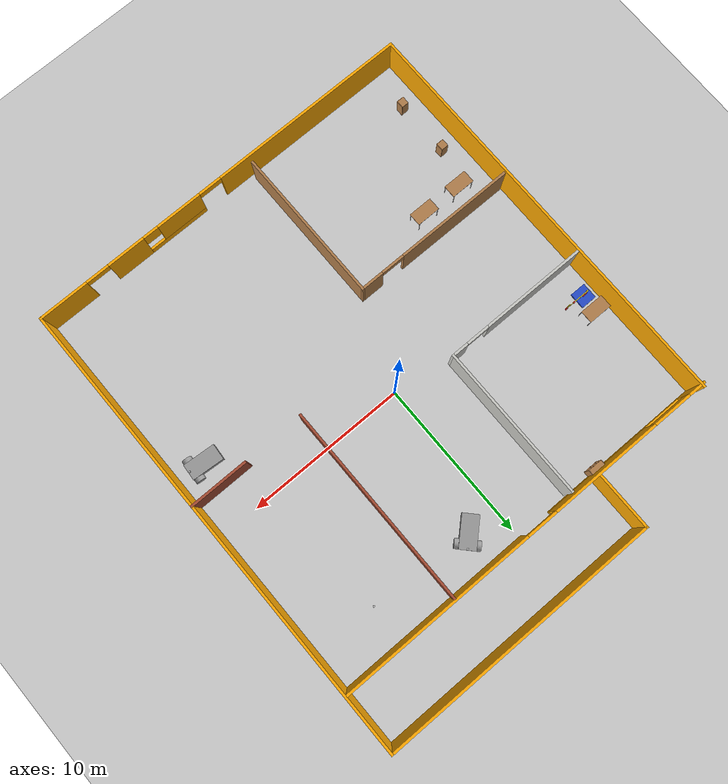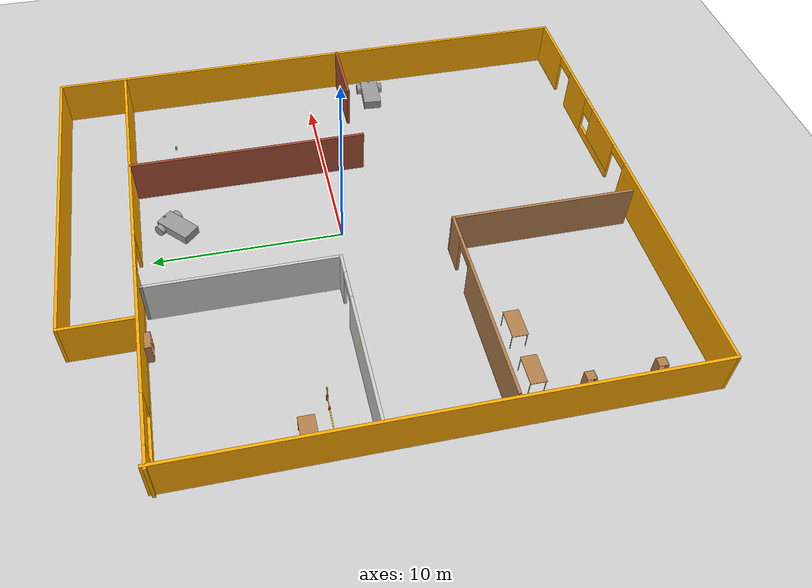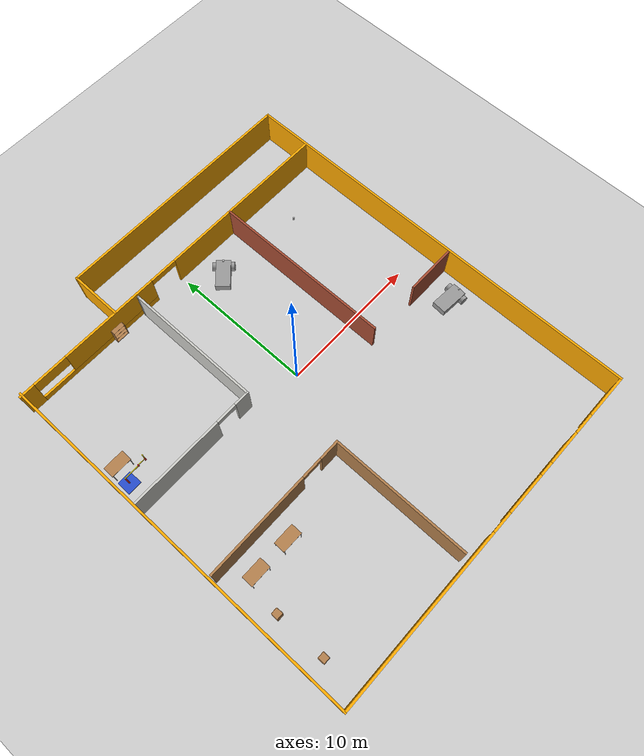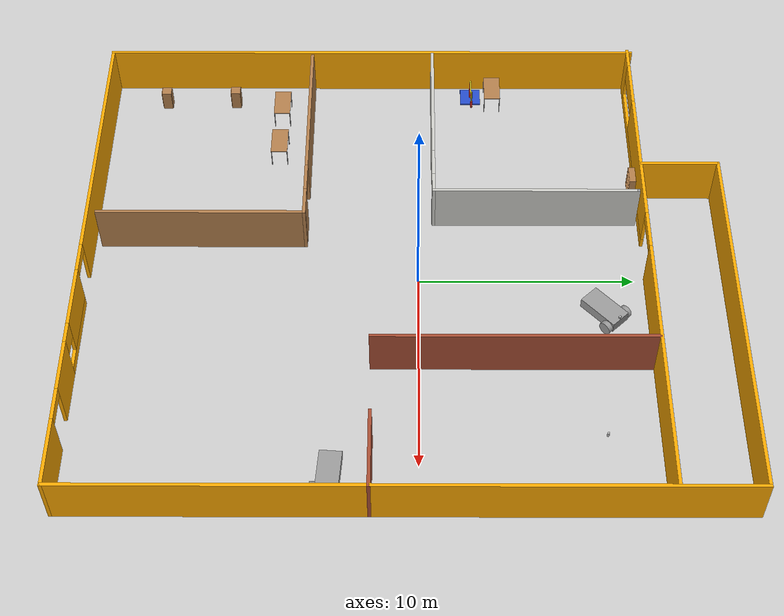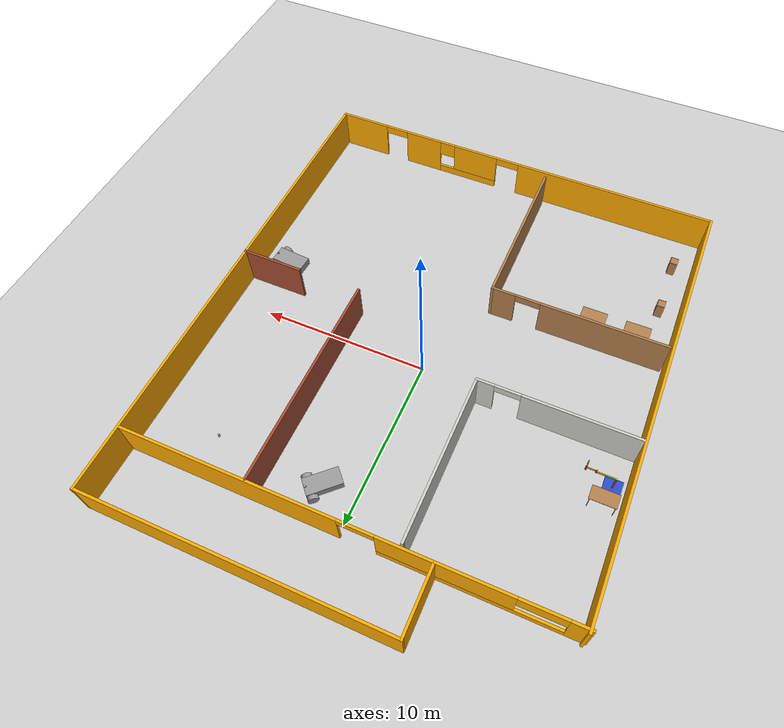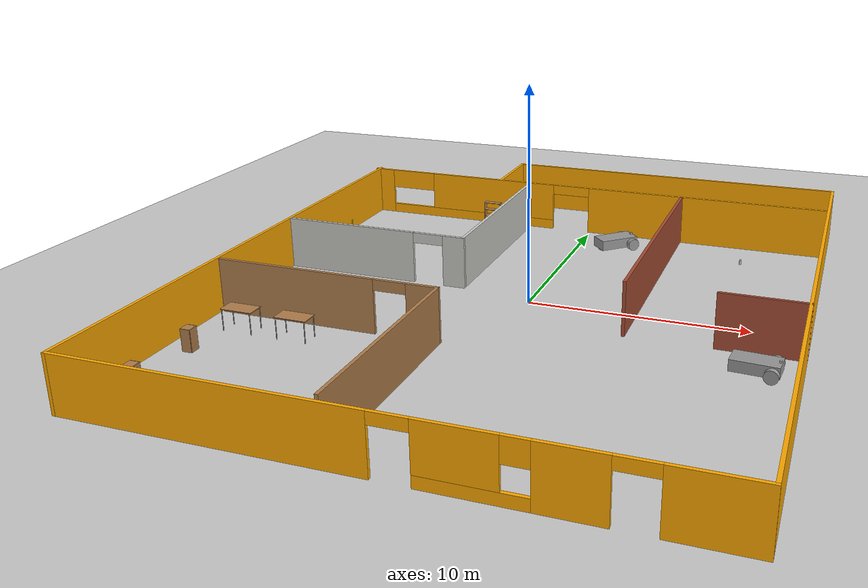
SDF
<sdf version="1.6">
 <world name="default">
  <plugin name="welcome" filename="libwelcome.so"/>
  <light name="sun" type="directional">
   <pose>0 0 10 0 -0 0</pose>
   <diffuse>0.8 0.8 0.8 1</diffuse>
   <specular>0.2 0.2 0.2 1</specular>
   <attenuation>
    <range>1000</range>
    <constant>0.9</constant>
    <linear>0.01</linear>
    <quadratic>0.001</quadratic>
   </attenuation>
   <direction>-0.5 0.1 -0.9</direction>
  </light>
  <model name="ground_plane">
   <static>1</static>
   <link name="link">
    <collision name="collision">
     <geometry><plane><normal>0 0 1</normal><size>100 100</size></plane></geometry>
     <surface>
      <contact><collide_bitmask>65535</collide_bitmask></contact>
      <friction><ode><mu>100</mu><mu2>50</mu2></ode></friction>
     </surface>
    </collision>
    <visual name="visual">
     <cast_shadows>0</cast_shadows>
     <geometry><plane><normal>0 0 1</normal><size>100 100</size></plane></geometry>
     <material>
      <script><uri>file://media/materials/scripts/gazebo.material</uri><name>Gazebo/Grey</name></script>
     </material>
    </visual>
   </link>
  </model>
  <gravity>0 0 -9.8</gravity>
  <magnetic_field>6e-06 2.3e-05 -4.2e-05</magnetic_field>
  <atmosphere type="adiabatic"/>
  <physics name="default_physics" default="0" type="ode">
   <max_step_size>0.001</max_step_size>
   <real_time_factor>1</real_time_factor>
   <real_time_update_rate>1000</real_time_update_rate>
  </physics>
  <scene><ambient>0.4 0.4 0.4 1</ambient><background>0.7 0.7 0.7 1</background><shadows>1</shadows></scene>
  <spherical_coordinates>
   <surface_model>EARTH_WGS84</surface_model>
   <latitude_deg>0</latitude_deg>
   <longitude_deg>0</longitude_deg>
   <elevation>0</elevation>
   <heading_deg>0</heading_deg>
  </spherical_coordinates>
  <model name="myhome">
   <pose>-0.234308 -0.560846 0 0 -0 0</pose>
   <link name="Wall_1">
    <collision name="Wall_1_Collision">
     <geometry><box><size>29.75 0.15 2.5</size></box></geometry>
     <pose>0 0 1.25 0 -0 0</pose>
    </collision>
    <visual name="Wall_1_Visual">
     <pose>0 0 1.25 0 -0 0</pose>
     <geometry><box><size>29.75 0.15 2.5</size></box></geometry>
     <material>
      <script><uri>file://media/materials/scripts/gazebo.material</uri><name>Gazebo/Grey</name></script>
      <ambient>1 0.666667 0 1</ambient>
     </material>
     <meta><layer>0</layer></meta>
    </visual>
    <pose>12.6114 0 0 0 0 -1.5708</pose>
   </link>
   <link name="Wall_10">
    <collision name="Wall_10_Collision">
     <geometry><box><size>12.75 0.15 2.5</size></box></geometry>
     <pose>0 0 1.25 0 -0 0</pose>
    </collision>
    <visual name="Wall_10_Visual">
     <pose>0 0 1.25 0 -0 0</pose>
     <geometry><box><size>12.75 0.15 2.5</size></box></geometry>
     <material>
      <script><uri>file://media/materials/scripts/gazebo.material</uri><name>Gazebo/Bricks</name></script>
      <ambient>1 1 1 1</ambient>
     </material>
     <meta><layer>0</layer></meta>
    </visual>
    <pose>5.14276 4.76599 0 0 -0 1.5708</pose>
   </link>
   <link name="Wall_12">
    <collision name="Wall_12_Collision">
     <geometry><box><size>9.75 0.15 2.5</size></box></geometry>
     <pose>0 0 1.25 0 -0 0</pose>
    </collision>
    <visual name="Wall_12_Visual">
     <pose>0 0 1.25 0 -0 0</pose>
     <geometry><box><size>9.75 0.15 2.5</size></box></geometry>
     <material>
      <script><uri>file://media/materials/scripts/gazebo.material</uri><name>Gazebo/CeilingTiled</name></script>
      <ambient>1 1 1 1</ambient>
     </material>
     <meta><layer>0</layer></meta>
    </visual>
    <pose>-3.26226 6.09462 0 0 0 -1.5708</pose>
   </link>
   <link name="Wall_13">
    <pose>-7.81226 1.29462 0 0 -0 3.14159</pose>
    <visual name="Wall_13_Visual_0">
     <pose>-4.07417 0 1.25 0 -0 0</pose>
     <geometry><box><size>1.10167 0.15 2.5</size></box></geometry>
     <material>
      <script><uri>file://media/materials/scripts/gazebo.material</uri><name>Gazebo/CeilingTiled</name></script>
      <ambient>1 1 1 1</ambient>
     </material>
     <meta><layer>0</layer></meta>
    </visual>
    <collision name="Wall_13_Collision_0">
     <geometry><box><size>1.10167 0.15 2.5</size></box></geometry>
     <pose>-4.07417 0 1.25 0 -0 0</pose>
    </collision>
    <visual name="Wall_13_Visual_1">
     <pose>1.30083 0 1.25 0 -0 0</pose>
     <geometry><box><size>6.64833 0.15 2.5</size></box></geometry>
     <material>
      <script><uri>file://media/materials/scripts/gazebo.material</uri><name>Gazebo/CeilingTiled</name></script>
      <ambient>1 1 1 1</ambient>
     </material>
     <meta><layer>0</layer></meta>
    </visual>
    <collision name="Wall_13_Collision_1">
     <geometry><box><size>6.64833 0.15 2.5</size></box></geometry>
     <pose>1.30083 0 1.25 0 -0 0</pose>
    </collision>
    <visual name="Wall_13_Visual_2">
     <pose>-2.77333 0 2.25 0 -0 0</pose>
     <geometry><box><size>1.5 0.15 0.5</size></box></geometry>
     <material>
      <script><uri>file://media/materials/scripts/gazebo.material</uri><name>Gazebo/CeilingTiled</name></script>
      <ambient>1 1 1 1</ambient>
     </material>
     <meta><layer>0</layer></meta>
    </visual>
    <collision name="Wall_13_Collision_2">
     <geometry><box><size>1.5 0.15 0.5</size></box></geometry>
     <pose>-2.77333 0 2.25 0 -0 0</pose>
    </collision>
   </link>
   <link name="Wall_15">
    <collision name="Wall_15_Collision">
     <geometry><box><size>9.75 0.15 2.5</size></box></geometry>
     <pose>0 0 1.25 0 -0 0</pose>
    </collision>
    <visual name="Wall_15_Visual">
     <pose>0 0 1.25 0 -0 0</pose>
     <geometry><box><size>9.75 0.15 2.5</size></box></geometry>
     <material>
      <script><uri>file://media/materials/scripts/gazebo.material</uri><name>Gazebo/Wood</name></script>
      <ambient>1 1 1 1</ambient>
     </material>
     <meta><layer>0</layer></meta>
    </visual>
    <pose>-1.91009 -9.54132 0 0 -0 1.5708</pose>
   </link>
   <link name="Wall_16">
    <pose>-7.08509 -4.74132 0 0 -0 3.14159</pose>
    <visual name="Wall_16_Visual_0">
     <pose>-4.50456 0 1.25 0 -0 0</pose>
     <geometry><box><size>1.49087 0.15 2.5</size></box></geometry>
     <material>
      <script><uri>file://media/materials/scripts/gazebo.material</uri><name>Gazebo/Wood</name></script>
      <ambient>1 1 1 1</ambient>
     </material>
     <meta><layer>0</layer></meta>
    </visual>
    <collision name="Wall_16_Collision_0">
     <geometry><box><size>1.49087 0.15 2.5</size></box></geometry>
     <pose>-4.50456 0 1.25 0 -0 0</pose>
    </collision>
    <visual name="Wall_16_Visual_1">
     <pose>1.49544 0 1.25 0 -0 0</pose>
     <geometry><box><size>7.50913 0.15 2.5</size></box></geometry>
     <material>
      <script><uri>file://media/materials/scripts/gazebo.material</uri><name>Gazebo/Wood</name></script>
      <ambient>1 1 1 1</ambient>
     </material>
     <meta><layer>0</layer></meta>
    </visual>
    <collision name="Wall_16_Collision_1">
     <geometry><box><size>7.50913 0.15 2.5</size></box></geometry>
     <pose>1.49544 0 1.25 0 -0 0</pose>
    </collision>
    <visual name="Wall_16_Visual_2">
     <pose>-3.00913 0 2.25 0 -0 0</pose>
     <geometry><box><size>1.5 0.15 0.5</size></box></geometry>
     <material>
      <script><uri>file://media/materials/scripts/gazebo.material</uri><name>Gazebo/Wood</name></script>
      <ambient>1 1 1 1</ambient>
     </material>
     <meta><layer>0</layer></meta>
    </visual>
    <collision name="Wall_16_Collision_2">
     <geometry><box><size>1.5 0.15 0.5</size></box></geometry>
     <pose>-3.00913 0 2.25 0 -0 0</pose>
    </collision>
   </link>
   <link name="Wall_18">
    <collision name="Wall_18_Collision">
     <geometry><box><size>0.15 0.15 2.5</size></box></geometry>
     <pose>0 0 1.25 0 -0 0</pose>
    </collision>
    <visual name="Wall_18_Visual">
     <pose>0 0 1.25 0 -0 0</pose>
     <geometry><box><size>0.15 0.15 2.5</size></box></geometry>
     <material>
      <script><uri>file://media/materials/scripts/gazebo.material</uri><name>Gazebo/Grey</name></script>
      <ambient>1 1 1 1</ambient>
     </material>
     <meta><layer>0</layer></meta>
    </visual>
    <pose>-3.26226 10.8946 0 0 -0 0</pose>
   </link>
   <link name="Wall_2">
    <pose>0.061369 -14.8 0 0 -0 3.14159</pose>
    <visual name="Wall_2_Visual_0">
     <pose>-11.0147 0 1.25 0 -0 0</pose>
     <geometry><box><size>3.22061 0.15 2.5</size></box></geometry>
     <material>
      <script><uri>file://media/materials/scripts/gazebo.material</uri><name>Gazebo/Grey</name></script>
      <ambient>1 0.666667 0 1</ambient>
     </material>
     <meta><layer>0</layer></meta>
    </visual>
    <collision name="Wall_2_Collision_0">
     <geometry><box><size>3.22061 0.15 2.5</size></box></geometry>
     <pose>-11.0147 0 1.25 0 -0 0</pose>
    </collision>
    <visual name="Wall_2_Visual_1">
     <pose>-6.67894 0 1.25 0 -0 0</pose>
     <geometry><box><size>2.4509 0.15 2.5</size></box></geometry>
     <material>
      <script><uri>file://media/materials/scripts/gazebo.material</uri><name>Gazebo/Grey</name></script>
      <ambient>1 0.666667 0 1</ambient>
     </material>
     <meta><layer>0</layer></meta>
    </visual>
    <collision name="Wall_2_Collision_1">
     <geometry><box><size>2.4509 0.15 2.5</size></box></geometry>
     <pose>-6.67894 0 1.25 0 -0 0</pose>
    </collision>
    <visual name="Wall_2_Visual_2">
     <pose>6.31564 0 1.25 0 -0 0</pose>
     <geometry><box><size>12.6187 0.15 2.5</size></box></geometry>
     <material>
      <script><uri>file://media/materials/scripts/gazebo.material</uri><name>Gazebo/Grey</name></script>
      <ambient>1 0.666667 0 1</ambient>
     </material>
     <meta><layer>0</layer></meta>
    </visual>
    <collision name="Wall_2_Collision_2">
     <geometry><box><size>12.6187 0.15 2.5</size></box></geometry>
     <pose>6.31564 0 1.25 0 -0 0</pose>
    </collision>
    <visual name="Wall_2_Visual_3">
     <pose>-3.47361 0 0.25 0 -0 0</pose>
     <geometry><box><size>3.95977 0.15 0.5</size></box></geometry>
     <material>
      <script><uri>file://media/materials/scripts/gazebo.material</uri><name>Gazebo/Grey</name></script>
      <ambient>1 0.666667 0 1</ambient>
     </material>
     <meta><layer>0</layer></meta>
    </visual>
    <collision name="Wall_2_Collision_3">
     <geometry><box><size>3.95977 0.15 0.5</size></box></geometry>
     <pose>-3.47361 0 0.25 0 -0 0</pose>
    </collision>
    <visual name="Wall_2_Visual_4">
     <pose>-2.97361 0 1.5 0 -0 0</pose>
     <geometry><box><size>2.95977 0.15 2</size></box></geometry>
     <material>
      <script><uri>file://media/materials/scripts/gazebo.material</uri><name>Gazebo/Grey</name></script>
      <ambient>1 0.666667 0 1</ambient>
     </material>
     <meta><layer>0</layer></meta>
    </visual>
    <collision name="Wall_2_Collision_4">
     <geometry><box><size>2.95977 0.15 2</size></box></geometry>
     <pose>-2.97361 0 1.5 0 -0 0</pose>
    </collision>
    <visual name="Wall_2_Visual_5">
     <pose>-4.95349 0 2 0 -0 0</pose>
     <geometry><box><size>1 0.15 1</size></box></geometry>
     <material>
      <script><uri>file://media/materials/scripts/gazebo.material</uri><name>Gazebo/Grey</name></script>
      <ambient>1 0.666667 0 1</ambient>
     </material>
     <meta><layer>0</layer></meta>
    </visual>
    <collision name="Wall_2_Collision_5">
     <geometry><box><size>1 0.15 1</size></box></geometry>
     <pose>-4.95349 0 2 0 -0 0</pose>
    </collision>
    <visual name="Wall_2_Visual_6">
     <pose>-8.65439 0 2.25 0 -0 0</pose>
     <geometry><box><size>1.5 0.15 0.5</size></box></geometry>
     <material>
      <script><uri>file://media/materials/scripts/gazebo.material</uri><name>Gazebo/Grey</name></script>
      <ambient>1 0.666667 0 1</ambient>
     </material>
     <meta><layer>0</layer></meta>
    </visual>
    <collision name="Wall_2_Collision_6">
     <geometry><box><size>1.5 0.15 0.5</size></box></geometry>
     <pose>-8.65439 0 2.25 0 -0 0</pose>
    </collision>
    <visual name="Wall_2_Visual_7">
     <pose>-0.743723 0 2.25 0 -0 0</pose>
     <geometry><box><size>1.5 0.15 0.5</size></box></geometry>
     <material>
      <script><uri>file://media/materials/scripts/gazebo.material</uri><name>Gazebo/Grey</name></script>
      <ambient>1 0.666667 0 1</ambient>
     </material>
     <meta><layer>0</layer></meta>
    </visual>
    <collision name="Wall_2_Collision_7">
     <geometry><box><size>1.5 0.15 0.5</size></box></geometry>
     <pose>-0.743723 0 2.25 0 -0 0</pose>
    </collision>
   </link>
   <link name="Wall_22">
    <collision name="Wall_22_Collision">
     <geometry><box><size>26.25 0.15 2.5</size></box></geometry>
     <pose>0 0 1.25 0 -0 0</pose>
    </collision>
    <visual name="Wall_22_Visual">
     <pose>0 0 1.25 0 -0 0</pose>
     <geometry><box><size>26.25 0.15 2.5</size></box></geometry>
     <material>
      <script><uri>file://media/materials/scripts/gazebo.material</uri><name>Gazebo/Grey</name></script>
      <ambient>1 0.666667 0 1</ambient>
     </material>
     <meta><layer>0</layer></meta>
    </visual>
    <pose>-12.4886 -1.75 0 0 -0 1.5708</pose>
   </link>
   <link name="Wall_24">
    <collision name="Wall_24_Collision">
     <geometry><box><size>17.75 0.15 2.5</size></box></geometry>
     <pose>0 0 1.25 0 -0 0</pose>
    </collision>
    <visual name="Wall_24_Visual">
     <pose>0 0 1.25 0 -0 0</pose>
     <geometry><box><size>17.75 0.15 2.5</size></box></geometry>
     <material>
      <script><uri>file://media/materials/scripts/gazebo.material</uri><name>Gazebo/Grey</name></script>
      <ambient>1 0.666667 0 1</ambient>
     </material>
     <meta><layer>0</layer></meta>
    </visual>
    <pose>3.81137 14.8 0 0 -0 3.14159</pose>
   </link>
   <link name="Wall_25">
    <collision name="Wall_25_Collision">
     <geometry><box><size>3.75 0.15 2.5</size></box></geometry>
     <pose>0 0 1.25 0 -0 0</pose>
    </collision>
    <visual name="Wall_25_Visual">
     <pose>0 0 1.25 0 -0 0</pose>
     <geometry><box><size>3.75 0.15 2.5</size></box></geometry>
     <material>
      <script><uri>file://media/materials/scripts/gazebo.material</uri><name>Gazebo/Grey</name></script>
      <ambient>1 0.666667 0 1</ambient>
     </material>
     <meta><layer>0</layer></meta>
    </visual>
    <pose>-4.98863 13 0 0 0 -1.5708</pose>
   </link>
   <link name="Wall_28">
    <collision name="Wall_28_Collision">
     <geometry><box><size>3.75 0.15 2.5</size></box></geometry>
     <pose>0 0 1.25 0 -0 0</pose>
    </collision>
    <visual name="Wall_28_Visual">
     <pose>0 0 1.25 0 -0 0</pose>
     <geometry><box><size>3.75 0.15 2.5</size></box></geometry>
     <material>
      <script><uri>file://media/materials/scripts/gazebo.material</uri><name>Gazebo/Bricks</name></script>
      <ambient>1 1 1 1</ambient>
     </material>
     <meta><layer>0</layer></meta>
    </visual>
    <pose>10.8145 -1.49857 0 0 -0 0</pose>
   </link>
   <link name="Wall_7">
    <pose>-0.064501 11.1407 0 0 -0 0</pose>
    <visual name="Wall_7_Visual_0">
     <pose>-12.0643 0 1.25 0 -0 0</pose>
     <geometry><box><size>1.1214 0.15 2.5</size></box></geometry>
     <material>
      <script><uri>file://media/materials/scripts/gazebo.material</uri><name>Gazebo/Grey</name></script>
      <ambient>1 0.666667 0 1</ambient>
     </material>
     <meta><layer>0</layer></meta>
    </visual>
    <collision name="Wall_7_Collision_0">
     <geometry><box><size>1.1214 0.15 2.5</size></box></geometry>
     <pose>-12.0643 0 1.25 0 -0 0</pose>
    </collision>
    <visual name="Wall_7_Visual_1">
     <pose>6.38957 0 1.25 0 -0 0</pose>
     <geometry><box><size>12.4709 0.15 2.5</size></box></geometry>
     <material>
      <script><uri>file://media/materials/scripts/gazebo.material</uri><name>Gazebo/Grey</name></script>
      <ambient>1 0.666667 0 1</ambient>
     </material>
     <meta><layer>0</layer></meta>
    </visual>
    <collision name="Wall_7_Collision_1">
     <geometry><box><size>12.4709 0.15 2.5</size></box></geometry>
     <pose>6.38957 0 1.25 0 -0 0</pose>
    </collision>
    <visual name="Wall_7_Visual_2">
     <pose>-6.67473 0 0.25 0 -0 0</pose>
     <geometry><box><size>9.65773 0.15 0.5</size></box></geometry>
     <material>
      <script><uri>file://media/materials/scripts/gazebo.material</uri><name>Gazebo/Grey</name></script>
      <ambient>1 0.666667 0 1</ambient>
     </material>
     <meta><layer>0</layer></meta>
    </visual>
    <collision name="Wall_7_Collision_2">
     <geometry><box><size>9.65773 0.15 0.5</size></box></geometry>
     <pose>-6.67473 0 0.25 0 -0 0</pose>
    </collision>
    <visual name="Wall_7_Visual_3">
     <pose>-5.42473 0 1.5 0 -0 0</pose>
     <geometry><box><size>7.15773 0.15 2</size></box></geometry>
     <material>
      <script><uri>file://media/materials/scripts/gazebo.material</uri><name>Gazebo/Grey</name></script>
      <ambient>1 0.666667 0 1</ambient>
     </material>
     <meta><layer>0</layer></meta>
    </visual>
    <collision name="Wall_7_Collision_3">
     <geometry><box><size>7.15773 0.15 2</size></box></geometry>
     <pose>-5.42473 0 1.5 0 -0 0</pose>
    </collision>
    <visual name="Wall_7_Visual_4">
     <pose>-10.2536 0 2 0 -0 0</pose>
     <geometry><box><size>2.5 0.15 1</size></box></geometry>
     <material>
      <script><uri>file://media/materials/scripts/gazebo.material</uri><name>Gazebo/Grey</name></script>
      <ambient>1 0.666667 0 1</ambient>
     </material>
     <meta><layer>0</layer></meta>
    </visual>
    <collision name="Wall_7_Collision_4">
     <geometry><box><size>2.5 0.15 1</size></box></geometry>
     <pose>-10.2536 0 2 0 -0 0</pose>
    </collision>
    <visual name="Wall_7_Visual_5">
     <pose>-0.845866 0 2.25 0 -0 0</pose>
     <geometry><box><size>2 0.15 0.5</size></box></geometry>
     <material>
      <script><uri>file://media/materials/scripts/gazebo.material</uri><name>Gazebo/Grey</name></script>
      <ambient>1 0.666667 0 1</ambient>
     </material>
     <meta><layer>0</layer></meta>
    </visual>
    <collision name="Wall_7_Collision_5">
     <geometry><box><size>2 0.15 0.5</size></box></geometry>
     <pose>-0.845866 0 2.25 0 -0 0</pose>
    </collision>
   </link>
   <static>1</static>
  </model>
  <model name="robot_car">
   <link name="link_1">
    <pose>-0.303354 -0.001131 0.03138 0 -0 0</pose>
    <inertial>
     <mass>1</mass>
     <inertia>
      <ixx>0.166667</ixx>
      <ixy>0</ixy>
      <ixz>0</ixz>
      <iyy>0.166667</iyy>
      <iyz>0</iyz>
      <izz>0.166667</izz>
     </inertia>
    </inertial>
    <visual name="visual">
     <geometry><box><size>2 1 0.5</size></box></geometry>
     <material>
      <lighting>1</lighting>
      <script><uri>file://media/materials/scripts/gazebo.material</uri><name>Gazebo/Grey</name></script>
      <shader type="pixel"><normal_map>__default__</normal_map></shader>
      <ambient>0.3 0.3 0.3 1</ambient>
      <diffuse>0.7 0.7 0.7 1</diffuse>
      <specular>0.01 0.01 0.01 1</specular>
      <emissive>0 0 0 1</emissive>
     </material>
    </visual>
    <collision name="collision">
     <geometry><box><size>2 1 0.5</size></box></geometry>
     <surface>
      <friction>
       <ode><mu>1</mu><mu2>1</mu2><fdir1>0 0 0</fdir1><slip1>0</slip1><slip2>0</slip2></ode>
       <torsional>
        <coefficient>1</coefficient>
        <patch_radius>0</patch_radius>
        <surface_radius>0</surface_radius>
        <use_patch_radius>1</use_patch_radius>
        <ode><slip>0</slip></ode>
       </torsional>
      </friction>
      <bounce><restitution_coefficient>0</restitution_coefficient><threshold>1e+06</threshold></bounce>
      <contact>
       <collide_without_contact>0</collide_without_contact>
       <collide_without_contact_bitmask>1</collide_without_contact_bitmask>
       <collide_bitmask>1</collide_bitmask>
       <ode>
        <soft_cfm>0</soft_cfm>
        <soft_erp>0.2</soft_erp>
        <kp>1e+13</kp>
        <kd>1</kd>
        <max_vel>0.01</max_vel>
        <min_depth>0</min_depth>
       </ode>
       <bullet>
        <split_impulse>1</split_impulse>
        <split_impulse_penetration_threshold>-0.01</split_impulse_penetration_threshold>
        <soft_cfm>0</soft_cfm>
        <soft_erp>0.2</soft_erp>
        <kp>1e+13</kp>
        <kd>1</kd>
       </bullet>
      </contact>
     </surface>
    </collision>
   </link>
   <link name="link_2">
    <pose>0.396646 -0.62616 -0.06862 1.5707 -0 0</pose>
    <inertial>
     <mass>1</mass>
     <inertia><ixx>0.145833</ixx><ixy>0</ixy><ixz>0</ixz><iyy>0.145833</iyy><iyz>0</iyz><izz>0.125</izz></inertia>
    </inertial>
    <visual name="visual">
     <geometry><cylinder><radius>0.3</radius><length>0.25</length></cylinder></geometry>
     <material>
      <lighting>1</lighting>
      <script><uri>file://media/materials/scripts/gazebo.material</uri><name>Gazebo/Grey</name></script>
      <shader type="pixel"><normal_map>__default__</normal_map></shader>
      <ambient>0.3 0.3 0.3 1</ambient>
      <diffuse>0.7 0.7 0.7 1</diffuse>
      <specular>0.01 0.01 0.01 1</specular>
      <emissive>0 0 0 1</emissive>
     </material>
    </visual>
    <collision name="collision">
     <geometry><cylinder><radius>0.3</radius><length>0.25</length></cylinder></geometry>
     <surface>
      <friction>
       <ode><mu>1</mu><mu2>1</mu2><fdir1>0 0 0</fdir1><slip1>0</slip1><slip2>0</slip2></ode>
       <torsional>
        <coefficient>1</coefficient>
        <patch_radius>0</patch_radius>
        <surface_radius>0</surface_radius>
        <use_patch_radius>1</use_patch_radius>
        <ode><slip>0</slip></ode>
       </torsional>
      </friction>
      <bounce><restitution_coefficient>0</restitution_coefficient><threshold>1e+06</threshold></bounce>
      <contact>
       <collide_without_contact>0</collide_without_contact>
       <collide_without_contact_bitmask>1</collide_without_contact_bitmask>
       <collide_bitmask>1</collide_bitmask>
       <ode>
        <soft_cfm>0</soft_cfm>
        <soft_erp>0.2</soft_erp>
        <kp>1e+13</kp>
        <kd>1</kd>
        <max_vel>0.01</max_vel>
        <min_depth>0</min_depth>
       </ode>
       <bullet>
        <split_impulse>1</split_impulse>
        <split_impulse_penetration_threshold>-0.01</split_impulse_penetration_threshold>
        <soft_cfm>0</soft_cfm>
        <soft_erp>0.2</soft_erp>
        <kp>1e+13</kp>
        <kd>1</kd>
       </bullet>
      </contact>
     </surface>
    </collision>
   </link>
   <link name="link_2_clone">
    <pose>0.396646 0.623898 -0.06862 1.5707 -0 0</pose>
    <inertial>
     <mass>1</mass>
     <inertia><ixx>0.145833</ixx><ixy>0</ixy><ixz>0</ixz><iyy>0.145833</iyy><iyz>0</iyz><izz>0.125</izz></inertia>
    </inertial>
    <visual name="visual">
     <geometry><cylinder><radius>0.3</radius><length>0.25</length></cylinder></geometry>
     <material>
      <lighting>1</lighting>
      <script><uri>file://media/materials/scripts/gazebo.material</uri><name>Gazebo/Grey</name></script>
      <shader type="pixel"><normal_map>__default__</normal_map></shader>
      <ambient>0.3 0.3 0.3 1</ambient>
      <diffuse>0.7 0.7 0.7 1</diffuse>
      <specular>0.01 0.01 0.01 1</specular>
      <emissive>0 0 0 1</emissive>
     </material>
    </visual>
    <collision name="collision">
     <geometry><cylinder><radius>0.3</radius><length>0.25</length></cylinder></geometry>
     <surface>
      <friction>
       <ode><mu>1</mu><mu2>1</mu2><fdir1>0 0 0</fdir1><slip1>0</slip1><slip2>0</slip2></ode>
       <torsional>
        <coefficient>1</coefficient>
        <patch_radius>0</patch_radius>
        <surface_radius>0</surface_radius>
        <use_patch_radius>1</use_patch_radius>
        <ode><slip>0</slip></ode>
       </torsional>
      </friction>
      <bounce><restitution_coefficient>0</restitution_coefficient><threshold>1e+06</threshold></bounce>
      <contact>
       <collide_without_contact>0</collide_without_contact>
       <collide_without_contact_bitmask>1</collide_without_contact_bitmask>
       <collide_bitmask>1</collide_bitmask>
       <ode>
        <soft_cfm>0</soft_cfm>
        <soft_erp>0.2</soft_erp>
        <kp>1e+13</kp>
        <kd>1</kd>
        <max_vel>0.01</max_vel>
        <min_depth>0</min_depth>
       </ode>
       <bullet>
        <split_impulse>1</split_impulse>
        <split_impulse_penetration_threshold>-0.01</split_impulse_penetration_threshold>
        <soft_cfm>0</soft_cfm>
        <soft_erp>0.2</soft_erp>
        <kp>1e+13</kp>
        <kd>1</kd>
       </bullet>
      </contact>
     </surface>
    </collision>
   </link>
   <link name="link_3">
    <pose>-1.10335 -0.001131 -0.16862 0 -0 0</pose>
    <inertial>
     <mass>1</mass>
     <inertia><ixx>0.1</ixx><ixy>0</ixy><ixz>0</ixz><iyy>0.1</iyy><iyz>0</iyz><izz>0.1</izz></inertia>
    </inertial>
    <visual name="visual">
     <geometry><sphere><radius>0.2</radius></sphere></geometry>
     <material>
      <lighting>1</lighting>
      <script><uri>file://media/materials/scripts/gazebo.material</uri><name>Gazebo/Grey</name></script>
      <shader type="pixel"><normal_map>__default__</normal_map></shader>
      <ambient>0.3 0.3 0.3 1</ambient>
      <diffuse>0.7 0.7 0.7 1</diffuse>
      <specular>0.01 0.01 0.01 1</specular>
      <emissive>0 0 0 1</emissive>
     </material>
    </visual>
    <collision name="collision">
     <geometry><sphere><radius>0.2</radius></sphere></geometry>
     <surface>
      <friction>
       <ode><mu>1</mu><mu2>1</mu2><fdir1>0 0 0</fdir1><slip1>0</slip1><slip2>0</slip2></ode>
       <torsional>
        <coefficient>1</coefficient>
        <patch_radius>0</patch_radius>
        <surface_radius>0</surface_radius>
        <use_patch_radius>1</use_patch_radius>
        <ode><slip>0</slip></ode>
       </torsional>
      </friction>
      <bounce><restitution_coefficient>0</restitution_coefficient><threshold>1e+06</threshold></bounce>
      <contact>
       <collide_without_contact>0</collide_without_contact>
       <collide_without_contact_bitmask>1</collide_without_contact_bitmask>
       <collide_bitmask>1</collide_bitmask>
       <ode>
        <soft_cfm>0</soft_cfm>
        <soft_erp>0.2</soft_erp>
        <kp>1e+13</kp>
        <kd>1</kd>
        <max_vel>0.01</max_vel>
        <min_depth>0</min_depth>
       </ode>
       <bullet>
        <split_impulse>1</split_impulse>
        <split_impulse_penetration_threshold>-0.01</split_impulse_penetration_threshold>
        <soft_cfm>0</soft_cfm>
        <soft_erp>0.2</soft_erp>
        <kp>1e+13</kp>
        <kd>1</kd>
       </bullet>
      </contact>
     </surface>
    </collision>
   </link>
   <model name="depth_camera">
    <link name="link">
     <pose>0 0 0.05 0 -0 0</pose>
     <inertial>
      <mass>0.1</mass>
      <inertia>
       <ixx>0.000166667</ixx>
       <iyy>0.000166667</iyy>
       <izz>0.000166667</izz>
       <ixy>0</ixy>
       <ixz>0</ixz>
       <iyz>0</iyz>
      </inertia>
     </inertial>
     <collision name="collision"><geometry><box><size>0.1 0.1 0.1</size></box></geometry></collision>
     <visual name="visual"><geometry><box><size>0.1 0.1 0.1</size></box></geometry></visual>
     <sensor name="camera" type="depth">
      <camera name="__default__">
       <horizontal_fov>1.047</horizontal_fov>
       <image><width>320</width><height>240</height></image>
       <clip><near>0.1</near><far>100</far></clip>
      </camera>
      <always_on>1</always_on>
      <update_rate>30</update_rate>
      <visualize>1</visualize>
     </sensor>
    </link>
    <pose>0.613416 0.004522 0.27448 0 -0 0</pose>
   </model>
   <joint name="link_1_JOINT_0" type="revolute">
    <parent>link_1</parent>
    <child>link_2</child>
    <axis>
     <xyz>0 0 1</xyz>
     <use_parent_model_frame>0</use_parent_model_frame>
     <limit>
      <lower>-1.79769e+308</lower>
      <upper>1.79769e+308</upper>
      <effort>-1</effort>
      <velocity>-1</velocity>
     </limit>
     <dynamics>
      <spring_reference>0</spring_reference>
      <spring_stiffness>0</spring_stiffness>
      <damping>0</damping>
     </dynamics>
    </axis>
    <physics>
     <ode><limit><cfm>0</cfm><erp>0.2</erp></limit><suspension><cfm>0</cfm><erp>0.2</erp></suspension></ode>
    </physics>
   </joint>
   <joint name="link_1_JOINT_1" type="revolute">
    <parent>link_1</parent>
    <child>link_2_clone</child>
    <axis>
     <xyz>0 0 1</xyz>
     <use_parent_model_frame>0</use_parent_model_frame>
     <limit>
      <lower>-1.79769e+308</lower>
      <upper>1.79769e+308</upper>
      <effort>-1</effort>
      <velocity>-1</velocity>
     </limit>
     <dynamics>
      <spring_reference>0</spring_reference>
      <spring_stiffness>0</spring_stiffness>
      <damping>0</damping>
     </dynamics>
    </axis>
    <physics>
     <ode><limit><cfm>0</cfm><erp>0.2</erp></limit><suspension><cfm>0</cfm><erp>0.2</erp></suspension></ode>
    </physics>
   </joint>
   <joint name="link_1_JOINT_3" type="ball">
    <parent>link_1</parent>
    <child>link_3</child>
    <physics>
     <ode><limit><cfm>0</cfm><erp>0.2</erp></limit><suspension><cfm>0</cfm><erp>0.2</erp></suspension></ode>
    </physics>
   </joint>
   <joint name="link_1_JOINT_5" type="fixed">
    <parent>link_1</parent>
    <child>depth_camera::link</child>
    <pose>0 0 0 0 -0.01 0</pose>
    <physics>
     <ode><limit><cfm>0</cfm><erp>0.2</erp></limit><suspension><cfm>0</cfm><erp>0.2</erp></suspension></ode>
    </physics>
   </joint>
   <static>0</static>
   <pose>10.9118 -3.83905 0.368627 4e-06 -6e-06 -0.074515</pose>
  </model>
  <model name="robot_car_0">
   <link name="link_1">
    <pose>-0.303354 -0.001131 0.03138 0 -0 0</pose>
    <inertial>
     <mass>1</mass>
     <inertia>
      <ixx>0.166667</ixx>
      <ixy>0</ixy>
      <ixz>0</ixz>
      <iyy>0.166667</iyy>
      <iyz>0</iyz>
      <izz>0.166667</izz>
     </inertia>
    </inertial>
    <visual name="visual">
     <geometry><box><size>2 1 0.5</size></box></geometry>
     <material>
      <lighting>1</lighting>
      <script><uri>file://media/materials/scripts/gazebo.material</uri><name>Gazebo/Grey</name></script>
      <shader type="pixel"><normal_map>__default__</normal_map></shader>
      <ambient>0.3 0.3 0.3 1</ambient>
      <diffuse>0.7 0.7 0.7 1</diffuse>
      <specular>0.01 0.01 0.01 1</specular>
      <emissive>0 0 0 1</emissive>
     </material>
    </visual>
    <collision name="collision">
     <geometry><box><size>2 1 0.5</size></box></geometry>
     <surface>
      <friction>
       <ode><mu>1</mu><mu2>1</mu2><fdir1>0 0 0</fdir1><slip1>0</slip1><slip2>0</slip2></ode>
       <torsional>
        <coefficient>1</coefficient>
        <patch_radius>0</patch_radius>
        <surface_radius>0</surface_radius>
        <use_patch_radius>1</use_patch_radius>
        <ode><slip>0</slip></ode>
       </torsional>
      </friction>
      <bounce><restitution_coefficient>0</restitution_coefficient><threshold>1e+06</threshold></bounce>
      <contact>
       <collide_without_contact>0</collide_without_contact>
       <collide_without_contact_bitmask>1</collide_without_contact_bitmask>
       <collide_bitmask>1</collide_bitmask>
       <ode>
        <soft_cfm>0</soft_cfm>
        <soft_erp>0.2</soft_erp>
        <kp>1e+13</kp>
        <kd>1</kd>
        <max_vel>0.01</max_vel>
        <min_depth>0</min_depth>
       </ode>
       <bullet>
        <split_impulse>1</split_impulse>
        <split_impulse_penetration_threshold>-0.01</split_impulse_penetration_threshold>
        <soft_cfm>0</soft_cfm>
        <soft_erp>0.2</soft_erp>
        <kp>1e+13</kp>
        <kd>1</kd>
       </bullet>
      </contact>
     </surface>
    </collision>
   </link>
   <link name="link_2">
    <pose>0.396646 -0.62616 -0.06862 1.5707 -0 0</pose>
    <inertial>
     <mass>1</mass>
     <inertia><ixx>0.145833</ixx><ixy>0</ixy><ixz>0</ixz><iyy>0.145833</iyy><iyz>0</iyz><izz>0.125</izz></inertia>
    </inertial>
    <visual name="visual">
     <geometry><cylinder><radius>0.3</radius><length>0.25</length></cylinder></geometry>
     <material>
      <lighting>1</lighting>
      <script><uri>file://media/materials/scripts/gazebo.material</uri><name>Gazebo/Grey</name></script>
      <shader type="pixel"><normal_map>__default__</normal_map></shader>
      <ambient>0.3 0.3 0.3 1</ambient>
      <diffuse>0.7 0.7 0.7 1</diffuse>
      <specular>0.01 0.01 0.01 1</specular>
      <emissive>0 0 0 1</emissive>
     </material>
    </visual>
    <collision name="collision">
     <geometry><cylinder><radius>0.3</radius><length>0.25</length></cylinder></geometry>
     <surface>
      <friction>
       <ode><mu>1</mu><mu2>1</mu2><fdir1>0 0 0</fdir1><slip1>0</slip1><slip2>0</slip2></ode>
       <torsional>
        <coefficient>1</coefficient>
        <patch_radius>0</patch_radius>
        <surface_radius>0</surface_radius>
        <use_patch_radius>1</use_patch_radius>
        <ode><slip>0</slip></ode>
       </torsional>
      </friction>
      <bounce><restitution_coefficient>0</restitution_coefficient><threshold>1e+06</threshold></bounce>
      <contact>
       <collide_without_contact>0</collide_without_contact>
       <collide_without_contact_bitmask>1</collide_without_contact_bitmask>
       <collide_bitmask>1</collide_bitmask>
       <ode>
        <soft_cfm>0</soft_cfm>
        <soft_erp>0.2</soft_erp>
        <kp>1e+13</kp>
        <kd>1</kd>
        <max_vel>0.01</max_vel>
        <min_depth>0</min_depth>
       </ode>
       <bullet>
        <split_impulse>1</split_impulse>
        <split_impulse_penetration_threshold>-0.01</split_impulse_penetration_threshold>
        <soft_cfm>0</soft_cfm>
        <soft_erp>0.2</soft_erp>
        <kp>1e+13</kp>
        <kd>1</kd>
       </bullet>
      </contact>
     </surface>
    </collision>
   </link>
   <link name="link_2_clone">
    <pose>0.396646 0.623898 -0.06862 1.5707 -0 0</pose>
    <inertial>
     <mass>1</mass>
     <inertia><ixx>0.145833</ixx><ixy>0</ixy><ixz>0</ixz><iyy>0.145833</iyy><iyz>0</iyz><izz>0.125</izz></inertia>
    </inertial>
    <visual name="visual">
     <geometry><cylinder><radius>0.3</radius><length>0.25</length></cylinder></geometry>
     <material>
      <lighting>1</lighting>
      <script><uri>file://media/materials/scripts/gazebo.material</uri><name>Gazebo/Grey</name></script>
      <shader type="pixel"><normal_map>__default__</normal_map></shader>
      <ambient>0.3 0.3 0.3 1</ambient>
      <diffuse>0.7 0.7 0.7 1</diffuse>
      <specular>0.01 0.01 0.01 1</specular>
      <emissive>0 0 0 1</emissive>
     </material>
    </visual>
    <collision name="collision">
     <geometry><cylinder><radius>0.3</radius><length>0.25</length></cylinder></geometry>
     <surface>
      <friction>
       <ode><mu>1</mu><mu2>1</mu2><fdir1>0 0 0</fdir1><slip1>0</slip1><slip2>0</slip2></ode>
       <torsional>
        <coefficient>1</coefficient>
        <patch_radius>0</patch_radius>
        <surface_radius>0</surface_radius>
        <use_patch_radius>1</use_patch_radius>
        <ode><slip>0</slip></ode>
       </torsional>
      </friction>
      <bounce><restitution_coefficient>0</restitution_coefficient><threshold>1e+06</threshold></bounce>
      <contact>
       <collide_without_contact>0</collide_without_contact>
       <collide_without_contact_bitmask>1</collide_without_contact_bitmask>
       <collide_bitmask>1</collide_bitmask>
       <ode>
        <soft_cfm>0</soft_cfm>
        <soft_erp>0.2</soft_erp>
        <kp>1e+13</kp>
        <kd>1</kd>
        <max_vel>0.01</max_vel>
        <min_depth>0</min_depth>
       </ode>
       <bullet>
        <split_impulse>1</split_impulse>
        <split_impulse_penetration_threshold>-0.01</split_impulse_penetration_threshold>
        <soft_cfm>0</soft_cfm>
        <soft_erp>0.2</soft_erp>
        <kp>1e+13</kp>
        <kd>1</kd>
       </bullet>
      </contact>
     </surface>
    </collision>
   </link>
   <link name="link_3">
    <pose>-1.10335 -0.001131 -0.16862 0 -0 0</pose>
    <inertial>
     <mass>1</mass>
     <inertia><ixx>0.1</ixx><ixy>0</ixy><ixz>0</ixz><iyy>0.1</iyy><iyz>0</iyz><izz>0.1</izz></inertia>
    </inertial>
    <visual name="visual">
     <geometry><sphere><radius>0.2</radius></sphere></geometry>
     <material>
      <lighting>1</lighting>
      <script><uri>file://media/materials/scripts/gazebo.material</uri><name>Gazebo/Grey</name></script>
      <shader type="pixel"><normal_map>__default__</normal_map></shader>
      <ambient>0.3 0.3 0.3 1</ambient>
      <diffuse>0.7 0.7 0.7 1</diffuse>
      <specular>0.01 0.01 0.01 1</specular>
      <emissive>0 0 0 1</emissive>
     </material>
    </visual>
    <collision name="collision">
     <geometry><sphere><radius>0.2</radius></sphere></geometry>
     <surface>
      <friction>
       <ode><mu>1</mu><mu2>1</mu2><fdir1>0 0 0</fdir1><slip1>0</slip1><slip2>0</slip2></ode>
       <torsional>
        <coefficient>1</coefficient>
        <patch_radius>0</patch_radius>
        <surface_radius>0</surface_radius>
        <use_patch_radius>1</use_patch_radius>
        <ode><slip>0</slip></ode>
       </torsional>
      </friction>
      <bounce><restitution_coefficient>0</restitution_coefficient><threshold>1e+06</threshold></bounce>
      <contact>
       <collide_without_contact>0</collide_without_contact>
       <collide_without_contact_bitmask>1</collide_without_contact_bitmask>
       <collide_bitmask>1</collide_bitmask>
       <ode>
        <soft_cfm>0</soft_cfm>
        <soft_erp>0.2</soft_erp>
        <kp>1e+13</kp>
        <kd>1</kd>
        <max_vel>0.01</max_vel>
        <min_depth>0</min_depth>
       </ode>
       <bullet>
        <split_impulse>1</split_impulse>
        <split_impulse_penetration_threshold>-0.01</split_impulse_penetration_threshold>
        <soft_cfm>0</soft_cfm>
        <soft_erp>0.2</soft_erp>
        <kp>1e+13</kp>
        <kd>1</kd>
       </bullet>
      </contact>
     </surface>
    </collision>
   </link>
   <model name="depth_camera">
    <link name="link">
     <pose>0 0 0.05 0 -0 0</pose>
     <inertial>
      <mass>0.1</mass>
      <inertia>
       <ixx>0.000166667</ixx>
       <iyy>0.000166667</iyy>
       <izz>0.000166667</izz>
       <ixy>0</ixy>
       <ixz>0</ixz>
       <iyz>0</iyz>
      </inertia>
     </inertial>
     <collision name="collision"><geometry><box><size>0.1 0.1 0.1</size></box></geometry></collision>
     <visual name="visual"><geometry><box><size>0.1 0.1 0.1</size></box></geometry></visual>
     <sensor name="camera" type="depth">
      <camera name="__default__">
       <horizontal_fov>1.047</horizontal_fov>
       <image><width>320</width><height>240</height></image>
       <clip><near>0.1</near><far>100</far></clip>
      </camera>
      <always_on>1</always_on>
      <update_rate>30</update_rate>
      <visualize>1</visualize>
     </sensor>
    </link>
    <pose>0.613416 0.004522 0.27448 0 -0 0</pose>
   </model>
   <joint name="link_1_JOINT_0" type="revolute">
    <parent>link_1</parent>
    <child>link_2</child>
    <axis>
     <xyz>0 0 1</xyz>
     <use_parent_model_frame>0</use_parent_model_frame>
     <limit>
      <lower>-1.79769e+308</lower>
      <upper>1.79769e+308</upper>
      <effort>-1</effort>
      <velocity>-1</velocity>
     </limit>
     <dynamics>
      <spring_reference>0</spring_reference>
      <spring_stiffness>0</spring_stiffness>
      <damping>0</damping>
     </dynamics>
    </axis>
    <physics>
     <ode><limit><cfm>0</cfm><erp>0.2</erp></limit><suspension><cfm>0</cfm><erp>0.2</erp></suspension></ode>
    </physics>
   </joint>
   <joint name="link_1_JOINT_1" type="revolute">
    <parent>link_1</parent>
    <child>link_2_clone</child>
    <axis>
     <xyz>0 0 1</xyz>
     <use_parent_model_frame>0</use_parent_model_frame>
     <limit>
      <lower>-1.79769e+308</lower>
      <upper>1.79769e+308</upper>
      <effort>-1</effort>
      <velocity>-1</velocity>
     </limit>
     <dynamics>
      <spring_reference>0</spring_reference>
      <spring_stiffness>0</spring_stiffness>
      <damping>0</damping>
     </dynamics>
    </axis>
    <physics>
     <ode><limit><cfm>0</cfm><erp>0.2</erp></limit><suspension><cfm>0</cfm><erp>0.2</erp></suspension></ode>
    </physics>
   </joint>
   <joint name="link_1_JOINT_3" type="ball">
    <parent>link_1</parent>
    <child>link_3</child>
    <physics>
     <ode><limit><cfm>0</cfm><erp>0.2</erp></limit><suspension><cfm>0</cfm><erp>0.2</erp></suspension></ode>
    </physics>
   </joint>
   <joint name="link_1_JOINT_5" type="fixed">
    <parent>link_1</parent>
    <child>depth_camera::link</child>
    <pose>0 0 0 0 -0.01 0</pose>
    <physics>
     <ode><limit><cfm>0</cfm><erp>0.2</erp></limit><suspension><cfm>0</cfm><erp>0.2</erp></suspension></ode>
    </physics>
   </joint>
   <static>0</static>
   <pose>2.13165 8.70709 0.368629 0 -8e-06 0.755658</pose>
  </model>
  <model name="bookshelf">
   <static>1</static>
   <link name="link">
    <inertial><mass>1</mass></inertial>
    <collision name="back">
     <pose>0 0.005 0.6 0 -0 0</pose>
     <geometry><box><size>0.9 0.01 1.2</size></box></geometry>
    </collision>
    <visual name="visual1">
     <pose>0 0.005 0.6 0 -0 0</pose>
     <geometry><box><size>0.9 0.01 1.2</size></box></geometry>
     <material>
      <script><uri>file://media/materials/scripts/gazebo.material</uri><name>Gazebo/Wood</name></script>
     </material>
    </visual>
    <collision name="left_side">
     <pose>0.45 -0.195 0.6 0 -0 0</pose>
     <geometry><box><size>0.02 0.4 1.2</size></box></geometry>
    </collision>
    <visual name="visual2">
     <pose>0.45 -0.195 0.6 0 -0 0</pose>
     <geometry><box><size>0.02 0.4 1.2</size></box></geometry>
     <material>
      <script><uri>file://media/materials/scripts/gazebo.material</uri><name>Gazebo/Wood</name></script>
     </material>
    </visual>
    <collision name="right_side">
     <pose>-0.45 -0.195 0.6 0 -0 0</pose>
     <geometry><box><size>0.02 0.4 1.2</size></box></geometry>
    </collision>
    <visual name="visual3">
     <pose>-0.45 -0.195 0.6 0 -0 0</pose>
     <geometry><box><size>0.02 0.4 1.2</size></box></geometry>
     <material>
      <script><uri>file://media/materials/scripts/gazebo.material</uri><name>Gazebo/Wood</name></script>
     </material>
    </visual>
    <collision name="bottom">
     <pose>0 -0.195 0.03 0 -0 0</pose>
     <geometry><box><size>0.88 0.4 0.06</size></box></geometry>
    </collision>
    <visual name="visual4">
     <pose>0 -0.195 0.03 0 -0 0</pose>
     <geometry><box><size>0.88 0.4 0.06</size></box></geometry>
     <material>
      <script><uri>file://media/materials/scripts/gazebo.material</uri><name>Gazebo/Wood</name></script>
     </material>
    </visual>
    <collision name="top">
     <pose>0 -0.195 1.19 0 -0 0</pose>
     <geometry><box><size>0.88 0.4 0.02</size></box></geometry>
    </collision>
    <visual name="visual5">
     <pose>0 -0.195 1.19 0 -0 0</pose>
     <geometry><box><size>0.88 0.4 0.02</size></box></geometry>
     <material>
      <script><uri>file://media/materials/scripts/gazebo.material</uri><name>Gazebo/Wood</name></script>
     </material>
    </visual>
    <collision name="low_shelf">
     <pose>0 -0.195 0.43 0 -0 0</pose>
     <geometry><box><size>0.88 0.4 0.02</size></box></geometry>
    </collision>
    <visual name="visual6">
     <pose>0 -0.195 0.43 0 -0 0</pose>
     <geometry><box><size>0.88 0.4 0.02</size></box></geometry>
     <material>
      <script><uri>file://media/materials/scripts/gazebo.material</uri><name>Gazebo/Wood</name></script>
     </material>
    </visual>
    <collision name="high_shelf">
     <pose>0 -0.195 0.8 0 -0 0</pose>
     <geometry><box><size>0.88 0.4 0.02</size></box></geometry>
    </collision>
    <visual name="visual7">
     <pose>0 -0.195 0.8 0 -0 0</pose>
     <geometry><box><size>0.88 0.4 0.02</size></box></geometry>
     <material>
      <script><uri>file://media/materials/scripts/gazebo.material</uri><name>Gazebo/Wood</name></script>
     </material>
    </visual>
   </link>
   <pose>-5.63915 10.5886 0 0 -0 0</pose>
  </model>
  <model name="beer">
   <link name="link">
    <pose>0 0 0.115 0 -0 0</pose>
    <inertial>
     <mass>0.39</mass>
     <inertia><ixx>0.00058</ixx><ixy>0</ixy><ixz>0</ixz><iyy>0.00058</iyy><iyz>0</iyz><izz>0.00019</izz></inertia>
    </inertial>
    <collision name="collision">
     <geometry><cylinder><radius>0.055</radius><length>0.23</length></cylinder></geometry>
    </collision>
    <visual name="visual">
     <geometry><cylinder><radius>0.055</radius><length>0.23</length></cylinder></geometry>
     <material>
      <script>
       <uri>model://beer/materials/scripts</uri>
       <uri>model://beer/materials/textures</uri>
       <name>Beer/Diffuse</name>
      </script>
     </material>
    </visual>
   </link>
   <pose>8.44687 8.20103 -2e-06 1e-06 -0 -2.1e-05</pose>
  </model>
  <model name="cabinet_1">
   <static>1</static>
   <link name="cabinet_bottom_plate">
    <inertial>
     <pose>0 0 -1 0 -0 0</pose>
     <inertia><ixx>2.05</ixx><ixy>0</ixy><ixz>0</ixz><iyy>2.05</iyy><iyz>0</iyz><izz>2.05</izz></inertia>
     <mass>25</mass>
    </inertial>
    <collision name="cabinet_bottom_plate_geom">
     <pose>0 0 0.01 0 -0 0</pose>
     <geometry><box><size>0.45 0.45 0.02</size></box></geometry>
    </collision>
    <visual name="cabinet_bottom_plate_geom_visual">
     <pose>0 0 0.01 0 -0 0</pose>
     <geometry><box><size>0.45 0.45 0.02</size></box></geometry>
     <material>
      <script><uri>file://media/materials/scripts/gazebo.material</uri><name>Gazebo/Wood</name></script>
     </material>
    </visual>
    <collision name="cabinet_bottom_plate_geom_cabinet_back_plate">
     <pose>0.235 0 0.51 0 -0 0</pose>
     <geometry><box><size>0.02 0.45 1.02</size></box></geometry>
    </collision>
    <visual name="cabinet_bottom_plate_geom_cabinet_back_plate_visual">
     <pose>0.235 0 0.51 0 -0 0</pose>
     <geometry><box><size>0.02 0.45 1.02</size></box></geometry>
     <material>
      <script><uri>file://media/materials/scripts/gazebo.material</uri><name>Gazebo/Wood</name></script>
     </material>
    </visual>
    <collision name="cabinet_bottom_plate_geom_cabinet_left_plate">
     <pose>0 0.235 0.51 0 -0 0</pose>
     <geometry><box><size>0.45 0.02 1.02</size></box></geometry>
    </collision>
    <visual name="cabinet_bottom_plate_geom_cabinet_left_plate_visual">
     <pose>0 0.235 0.51 0 -0 0</pose>
     <geometry><box><size>0.45 0.02 1.02</size></box></geometry>
     <material>
      <script><uri>file://media/materials/scripts/gazebo.material</uri><name>Gazebo/Wood</name></script>
     </material>
    </visual>
    <collision name="cabinet_bottom_plate_geom_cabinet_middle_plate">
     <pose>0 0 0.51 0 -0 0</pose>
     <geometry><box><size>0.45 0.45 0.02</size></box></geometry>
    </collision>
    <visual name="cabinet_bottom_plate_geom_cabinet_middle_plate_visual">
     <pose>0 0 0.51 0 -0 0</pose>
     <geometry><box><size>0.45 0.45 0.02</size></box></geometry>
     <material>
      <script><uri>file://media/materials/scripts/gazebo.material</uri><name>Gazebo/Wood</name></script>
     </material>
    </visual>
    <collision name="cabinet_bottom_plate_geom_cabinet_right_plate">
     <pose>0 -0.235 0.51 0 -0 0</pose>
     <geometry><box><size>0.45 0.02 1.02</size></box></geometry>
    </collision>
    <visual name="cabinet_bottom_plate_geom_cabinet_right_plate_visual">
     <pose>0 -0.235 0.51 0 -0 0</pose>
     <geometry><box><size>0.45 0.02 1.02</size></box></geometry>
     <material>
      <script><uri>file://media/materials/scripts/gazebo.material</uri><name>Gazebo/Wood</name></script>
     </material>
    </visual>
    <collision name="cabinet_bottom_plate_geom_cabinet_top_plate">
     <pose>0 0 1.01 0 -0 0</pose>
     <geometry><box><size>0.45 0.45 0.02</size></box></geometry>
    </collision>
    <visual name="cabinet_bottom_plate_geom_cabinet_top_plate_visual">
     <pose>0 0 1.01 0 -0 0</pose>
     <geometry><box><size>0.45 0.45 0.02</size></box></geometry>
     <material>
      <script><uri>file://media/materials/scripts/gazebo.material</uri><name>Gazebo/Wood</name></script>
     </material>
    </visual>
   </link>
   <pose>-11.4912 -9.22779 0 0 -0 0</pose>
  </model>
  <model name="cabinet_2">
   <static>1</static>
   <link name="cabinet_bottom_plate">
    <inertial>
     <pose>0 0 -1 0 -0 0</pose>
     <inertia><ixx>2.05</ixx><ixy>0</ixy><ixz>0</ixz><iyy>2.05</iyy><iyz>0</iyz><izz>2.05</izz></inertia>
     <mass>25</mass>
    </inertial>
    <collision name="cabinet_bottom_plate_geom">
     <pose>0 0 0.01 0 -0 0</pose>
     <geometry><box><size>0.45 0.45 0.02</size></box></geometry>
    </collision>
    <visual name="cabinet_bottom_plate_geom_visual">
     <pose>0 0 0.01 0 -0 0</pose>
     <geometry><box><size>0.45 0.45 0.02</size></box></geometry>
     <material>
      <script><uri>file://media/materials/scripts/gazebo.material</uri><name>Gazebo/Wood</name></script>
     </material>
    </visual>
    <collision name="cabinet_bottom_plate_geom_cabinet_back_plate">
     <pose>0.235 0 0.51 0 -0 0</pose>
     <geometry><box><size>0.02 0.45 1.02</size></box></geometry>
    </collision>
    <visual name="cabinet_bottom_plate_geom_cabinet_back_plate_visual">
     <pose>0.235 0 0.51 0 -0 0</pose>
     <geometry><box><size>0.02 0.45 1.02</size></box></geometry>
     <material>
      <script><uri>file://media/materials/scripts/gazebo.material</uri><name>Gazebo/Wood</name></script>
     </material>
    </visual>
    <collision name="cabinet_bottom_plate_geom_cabinet_left_plate">
     <pose>0 0.235 0.51 0 -0 0</pose>
     <geometry><box><size>0.45 0.02 1.02</size></box></geometry>
    </collision>
    <visual name="cabinet_bottom_plate_geom_cabinet_left_plate_visual">
     <pose>0 0.235 0.51 0 -0 0</pose>
     <geometry><box><size>0.45 0.02 1.02</size></box></geometry>
     <material>
      <script><uri>file://media/materials/scripts/gazebo.material</uri><name>Gazebo/Wood</name></script>
     </material>
    </visual>
    <collision name="cabinet_bottom_plate_geom_cabinet_middle_plate">
     <pose>0 0 0.51 0 -0 0</pose>
     <geometry><box><size>0.45 0.45 0.02</size></box></geometry>
    </collision>
    <visual name="cabinet_bottom_plate_geom_cabinet_middle_plate_visual">
     <pose>0 0 0.51 0 -0 0</pose>
     <geometry><box><size>0.45 0.45 0.02</size></box></geometry>
     <material>
      <script><uri>file://media/materials/scripts/gazebo.material</uri><name>Gazebo/Wood</name></script>
     </material>
    </visual>
    <collision name="cabinet_bottom_plate_geom_cabinet_right_plate">
     <pose>0 -0.235 0.51 0 -0 0</pose>
     <geometry><box><size>0.45 0.02 1.02</size></box></geometry>
    </collision>
    <visual name="cabinet_bottom_plate_geom_cabinet_right_plate_visual">
     <pose>0 -0.235 0.51 0 -0 0</pose>
     <geometry><box><size>0.45 0.02 1.02</size></box></geometry>
     <material>
      <script><uri>file://media/materials/scripts/gazebo.material</uri><name>Gazebo/Wood</name></script>
     </material>
    </visual>
    <collision name="cabinet_bottom_plate_geom_cabinet_top_plate">
     <pose>0 0 1.01 0 -0 0</pose>
     <geometry><box><size>0.45 0.45 0.02</size></box></geometry>
    </collision>
    <visual name="cabinet_bottom_plate_geom_cabinet_top_plate_visual">
     <pose>0 0 1.01 0 -0 0</pose>
     <geometry><box><size>0.45 0.45 0.02</size></box></geometry>
     <material>
      <script><uri>file://media/materials/scripts/gazebo.material</uri><name>Gazebo/Wood</name></script>
     </material>
    </visual>
   </link>
   <pose>-11.4499 -12.7184 0 0 -0 0</pose>
  </model>
  <model name="table">
   <static>1</static>
   <link name="link">
    <collision name="surface">
     <pose>0 0 1 0 -0 0</pose>
     <geometry><box><size>1.5 0.8 0.03</size></box></geometry>
     <surface><friction><ode><mu>0.6</mu><mu2>0.6</mu2></ode></friction></surface>
    </collision>
    <visual name="visual1">
     <pose>0 0 1 0 -0 0</pose>
     <geometry><box><size>1.5 0.8 0.03</size></box></geometry>
     <material>
      <script><uri>file://media/materials/scripts/gazebo.material</uri><name>Gazebo/Wood</name></script>
     </material>
    </visual>
    <collision name="front_left_leg">
     <pose>0.68 0.38 0.5 0 -0 0</pose>
     <geometry><cylinder><radius>0.02</radius><length>1</length></cylinder></geometry>
    </collision>
    <visual name="front_left_leg">
     <pose>0.68 0.38 0.5 0 -0 0</pose>
     <geometry><cylinder><radius>0.02</radius><length>1</length></cylinder></geometry>
     <material>
      <script><uri>file://media/materials/scripts/gazebo.material</uri><name>Gazebo/Grey</name></script>
     </material>
    </visual>
    <collision name="front_right_leg">
     <pose>0.68 -0.38 0.5 0 -0 0</pose>
     <geometry><cylinder><radius>0.02</radius><length>1</length></cylinder></geometry>
    </collision>
    <visual name="front_right_leg">
     <pose>0.68 -0.38 0.5 0 -0 0</pose>
     <geometry><cylinder><radius>0.02</radius><length>1</length></cylinder></geometry>
     <material>
      <script><uri>file://media/materials/scripts/gazebo.material</uri><name>Gazebo/Grey</name></script>
     </material>
    </visual>
    <collision name="back_right_leg">
     <pose>-0.68 -0.38 0.5 0 -0 0</pose>
     <geometry><cylinder><radius>0.02</radius><length>1</length></cylinder></geometry>
    </collision>
    <visual name="back_right_leg">
     <pose>-0.68 -0.38 0.5 0 -0 0</pose>
     <geometry><cylinder><radius>0.02</radius><length>1</length></cylinder></geometry>
     <material>
      <script><uri>file://media/materials/scripts/gazebo.material</uri><name>Gazebo/Grey</name></script>
     </material>
    </visual>
    <collision name="back_left_leg">
     <pose>-0.68 0.38 0.5 0 -0 0</pose>
     <geometry><cylinder><radius>0.02</radius><length>1</length></cylinder></geometry>
    </collision>
    <visual name="back_left_leg">
     <pose>-0.68 0.38 0.5 0 -0 0</pose>
     <geometry><cylinder><radius>0.02</radius><length>1</length></cylinder></geometry>
     <material>
      <script><uri>file://media/materials/scripts/gazebo.material</uri><name>Gazebo/Grey</name></script>
     </material>
    </visual>
   </link>
   <pose>-8.03014 -6.81331 0 0 -0 0</pose>
  </model>
  <model name="simple_arm">
   <link name="arm_base">
    <inertial>
     <pose>0 0 0.00099 0 -0 0</pose>
     <inertia><ixx>1.11</ixx><ixy>0</ixy><ixz>0</ixz><iyy>100.11</iyy><iyz>0</iyz><izz>1.01</izz></inertia>
     <mass>101</mass>
    </inertial>
    <collision name="arm_base_geom">
     <pose>0 0 0.05 0 -0 0</pose>
     <geometry><box><size>1 1 0.1</size></box></geometry>
    </collision>
    <visual name="arm_base_geom_visual">
     <pose>0 0 0.05 0 -0 0</pose>
     <geometry><box><size>1 1 0.1</size></box></geometry>
     <material>
      <script><uri>file://media/materials/scripts/gazebo.material</uri><name>Gazebo/Blue</name></script>
     </material>
    </visual>
    <collision name="arm_base_geom_arm_trunk">
     <pose>0 0 0.6 0 -0 0</pose>
     <geometry><cylinder><radius>0.05</radius><length>1</length></cylinder></geometry>
    </collision>
    <visual name="arm_base_geom_arm_trunk_visual">
     <pose>0 0 0.6 0 -0 0</pose>
     <geometry><cylinder><radius>0.05</radius><length>1</length></cylinder></geometry>
     <material>
      <script><uri>file://media/materials/scripts/gazebo.material</uri><name>Gazebo/Red</name></script>
     </material>
    </visual>
   </link>
   <link name="arm_shoulder_pan">
    <pose>0 0 1.1 0 -0 0</pose>
    <inertial>
     <pose>0.045455 0 0 0 -0 0</pose>
     <inertia><ixx>0.011</ixx><ixy>0</ixy><ixz>0</ixz><iyy>0.0225</iyy><iyz>0</iyz><izz>0.0135</izz></inertia>
     <mass>1.1</mass>
    </inertial>
    <collision name="arm_shoulder_pan_geom">
     <pose>0 0 0.05 0 -0 0</pose>
     <geometry><cylinder><radius>0.05</radius><length>0.1</length></cylinder></geometry>
    </collision>
    <visual name="arm_shoulder_pan_geom_visual">
     <pose>0 0 0.05 0 -0 0</pose>
     <geometry><cylinder><radius>0.05</radius><length>0.1</length></cylinder></geometry>
     <material>
      <script><uri>file://media/materials/scripts/gazebo.material</uri><name>Gazebo/Yellow</name></script>
     </material>
    </visual>
    <collision name="arm_shoulder_pan_geom_arm_shoulder">
     <pose>0.55 0 0.05 0 -0 0</pose>
     <geometry><box><size>1 0.05 0.1</size></box></geometry>
    </collision>
    <visual name="arm_shoulder_pan_geom_arm_shoulder_visual">
     <pose>0.55 0 0.05 0 -0 0</pose>
     <geometry><box><size>1 0.05 0.1</size></box></geometry>
     <material>
      <script><uri>file://media/materials/scripts/gazebo.material</uri><name>Gazebo/Yellow</name></script>
     </material>
    </visual>
   </link>
   <link name="arm_elbow_pan">
    <pose>1.05 0 1.1 0 -0 0</pose>
    <inertial>
     <pose>0.0875 0 0.083333 0 -0 0</pose>
     <inertia>
      <ixx>0.031</ixx>
      <ixy>0</ixy>
      <ixz>0.005</ixz>
      <iyy>0.07275</iyy>
      <iyz>0</iyz>
      <izz>0.04475</izz>
     </inertia>
     <mass>1.2</mass>
    </inertial>
    <collision name="arm_elbow_pan_geom">
     <pose>0 0 0.1 0 -0 0</pose>
     <geometry><cylinder><radius>0.05</radius><length>0.2</length></cylinder></geometry>
    </collision>
    <visual name="arm_elbow_pan_geom_visual">
     <pose>0 0 0.1 0 -0 0</pose>
     <geometry><cylinder><radius>0.05</radius><length>0.2</length></cylinder></geometry>
     <material>
      <script><uri>file://media/materials/scripts/gazebo.material</uri><name>Gazebo/Red</name></script>
     </material>
    </visual>
    <collision name="arm_elbow_pan_geom_arm_elbow">
     <pose>0.3 0 0.15 0 -0 0</pose>
     <geometry><box><size>0.5 0.03 0.1</size></box></geometry>
    </collision>
    <visual name="arm_elbow_pan_geom_arm_elbow_visual">
     <pose>0.3 0 0.15 0 -0 0</pose>
     <geometry><box><size>0.5 0.03 0.1</size></box></geometry>
     <material>
      <script><uri>file://media/materials/scripts/gazebo.material</uri><name>Gazebo/Yellow</name></script>
     </material>
    </visual>
    <collision name="arm_elbow_pan_geom_arm_wrist">
     <pose>0.55 0 0.15 0 -0 0</pose>
     <geometry><cylinder><radius>0.05</radius><length>0.3</length></cylinder></geometry>
    </collision>
    <visual name="arm_elbow_pan_geom_arm_wrist_visual">
     <pose>0.55 0 0.15 0 -0 0</pose>
     <geometry><cylinder><radius>0.05</radius><length>0.3</length></cylinder></geometry>
     <material>
      <script><uri>file://media/materials/scripts/gazebo.material</uri><name>Gazebo/Red</name></script>
     </material>
    </visual>
   </link>
   <link name="arm_wrist_lift">
    <pose>1.6 0 1.05 0 -0 0</pose>
    <inertial>
     <inertia><ixx>0.01</ixx><ixy>0</ixy><ixz>0</ixz><iyy>0.01</iyy><iyz>0</iyz><izz>0.001</izz></inertia>
     <mass>0.1</mass>
    </inertial>
    <collision name="arm_wrist_lift_geom">
     <pose>0 0 0.5 0 -0 0</pose>
     <geometry><cylinder><radius>0.03</radius><length>1</length></cylinder></geometry>
    </collision>
    <visual name="arm_wrist_lift_geom_visual">
     <pose>0 0 0.5 0 -0 0</pose>
     <geometry><cylinder><radius>0.03</radius><length>1</length></cylinder></geometry>
     <material>
      <script><uri>file://media/materials/scripts/gazebo.material</uri><name>Gazebo/Yellow</name></script>
     </material>
    </visual>
   </link>
   <link name="arm_wrist_roll">
    <pose>1.6 0 1 0 -0 0</pose>
    <inertial>
     <inertia><ixx>0.01</ixx><ixy>0</ixy><ixz>0</ixz><iyy>0.01</iyy><iyz>0</iyz><izz>0.001</izz></inertia>
     <mass>0.1</mass>
    </inertial>
    <collision name="arm_wrist_roll_geom">
     <pose>0 0 0.025 0 -0 0</pose>
     <geometry><cylinder><radius>0.05</radius><length>0.05</length></cylinder></geometry>
    </collision>
    <visual name="arm_wrist_roll_geom_visual">
     <pose>0 0 0.025 0 -0 0</pose>
     <geometry><cylinder><radius>0.05</radius><length>0.05</length></cylinder></geometry>
     <material>
      <script><uri>file://media/materials/scripts/gazebo.material</uri><name>Gazebo/Red</name></script>
     </material>
    </visual>
   </link>
   <joint name="arm_shoulder_pan_joint" type="revolute">
    <parent>arm_base</parent>
    <child>arm_shoulder_pan</child>
    <axis>
     <dynamics>
      <damping>1</damping>
      <friction>0</friction>
      <spring_reference>0</spring_reference>
      <spring_stiffness>0</spring_stiffness>
     </dynamics>
     <xyz>0 0 1</xyz>
     <use_parent_model_frame>1</use_parent_model_frame>
     <limit><lower>-1e+16</lower><upper>1e+16</upper></limit>
    </axis>
   </joint>
   <joint name="arm_elbow_pan_joint" type="revolute">
    <parent>arm_shoulder_pan</parent>
    <child>arm_elbow_pan</child>
    <axis>
     <dynamics>
      <damping>1</damping>
      <friction>0</friction>
      <spring_reference>0</spring_reference>
      <spring_stiffness>0</spring_stiffness>
     </dynamics>
     <xyz>0 0 1</xyz>
     <use_parent_model_frame>1</use_parent_model_frame>
     <limit><lower>-1e+16</lower><upper>1e+16</upper></limit>
    </axis>
   </joint>
   <joint name="arm_wrist_lift_joint" type="prismatic">
    <parent>arm_elbow_pan</parent>
    <child>arm_wrist_lift</child>
    <axis>
     <dynamics>
      <damping>1</damping>
      <friction>0</friction>
      <spring_reference>0</spring_reference>
      <spring_stiffness>0</spring_stiffness>
     </dynamics>
     <limit><lower>-0.8</lower><upper>0.1</upper></limit>
     <xyz>0 0 1</xyz>
     <use_parent_model_frame>1</use_parent_model_frame>
    </axis>
   </joint>
   <joint name="arm_wrist_roll_joint" type="revolute">
    <parent>arm_wrist_lift</parent>
    <child>arm_wrist_roll</child>
    <axis>
     <dynamics>
      <damping>1</damping>
      <friction>0</friction>
      <spring_reference>0</spring_reference>
      <spring_stiffness>0</spring_stiffness>
     </dynamics>
     <limit><lower>-2.99999</lower><upper>2.99999</upper></limit>
     <xyz>0 0 1</xyz>
     <use_parent_model_frame>1</use_parent_model_frame>
    </axis>
   </joint>
   <pose>-11.956 2.69436 0 0 0 -0.000907</pose>
  </model>
  <model name="table_0">
   <static>1</static>
   <link name="link">
    <collision name="surface">
     <pose>0 0 1 0 -0 0</pose>
     <geometry><box><size>1.5 0.8 0.03</size></box></geometry>
     <surface><friction><ode><mu>0.6</mu><mu2>0.6</mu2></ode></friction></surface>
    </collision>
    <visual name="visual1">
     <pose>0 0 1 0 -0 0</pose>
     <geometry><box><size>1.5 0.8 0.03</size></box></geometry>
     <material>
      <script><uri>file://media/materials/scripts/gazebo.material</uri><name>Gazebo/Wood</name></script>
     </material>
    </visual>
    <collision name="front_left_leg">
     <pose>0.68 0.38 0.5 0 -0 0</pose>
     <geometry><cylinder><radius>0.02</radius><length>1</length></cylinder></geometry>
    </collision>
    <visual name="front_left_leg">
     <pose>0.68 0.38 0.5 0 -0 0</pose>
     <geometry><cylinder><radius>0.02</radius><length>1</length></cylinder></geometry>
     <material>
      <script><uri>file://media/materials/scripts/gazebo.material</uri><name>Gazebo/Grey</name></script>
     </material>
    </visual>
    <collision name="front_right_leg">
     <pose>0.68 -0.38 0.5 0 -0 0</pose>
     <geometry><cylinder><radius>0.02</radius><length>1</length></cylinder></geometry>
    </collision>
    <visual name="front_right_leg">
     <pose>0.68 -0.38 0.5 0 -0 0</pose>
     <geometry><cylinder><radius>0.02</radius><length>1</length></cylinder></geometry>
     <material>
      <script><uri>file://media/materials/scripts/gazebo.material</uri><name>Gazebo/Grey</name></script>
     </material>
    </visual>
    <collision name="back_right_leg">
     <pose>-0.68 -0.38 0.5 0 -0 0</pose>
     <geometry><cylinder><radius>0.02</radius><length>1</length></cylinder></geometry>
    </collision>
    <visual name="back_right_leg">
     <pose>-0.68 -0.38 0.5 0 -0 0</pose>
     <geometry><cylinder><radius>0.02</radius><length>1</length></cylinder></geometry>
     <material>
      <script><uri>file://media/materials/scripts/gazebo.material</uri><name>Gazebo/Grey</name></script>
     </material>
    </visual>
    <collision name="back_left_leg">
     <pose>-0.68 0.38 0.5 0 -0 0</pose>
     <geometry><cylinder><radius>0.02</radius><length>1</length></cylinder></geometry>
    </collision>
    <visual name="back_left_leg">
     <pose>-0.68 0.38 0.5 0 -0 0</pose>
     <geometry><cylinder><radius>0.02</radius><length>1</length></cylinder></geometry>
     <material>
      <script><uri>file://media/materials/scripts/gazebo.material</uri><name>Gazebo/Grey</name></script>
     </material>
    </visual>
   </link>
   <pose>-11.6764 3.7629 0 0 -0 0</pose>
  </model>
  <model name="table_1">
   <static>1</static>
   <link name="link">
    <collision name="surface">
     <pose>0 0 1 0 -0 0</pose>
     <geometry><box><size>1.5 0.8 0.03</size></box></geometry>
     <surface><friction><ode><mu>0.6</mu><mu2>0.6</mu2></ode></friction></surface>
    </collision>
    <visual name="visual1">
     <pose>0 0 1 0 -0 0</pose>
     <geometry><box><size>1.5 0.8 0.03</size></box></geometry>
     <material>
      <script><uri>file://media/materials/scripts/gazebo.material</uri><name>Gazebo/Wood</name></script>
     </material>
    </visual>
    <collision name="front_left_leg">
     <pose>0.68 0.38 0.5 0 -0 0</pose>
     <geometry><cylinder><radius>0.02</radius><length>1</length></cylinder></geometry>
    </collision>
    <visual name="front_left_leg">
     <pose>0.68 0.38 0.5 0 -0 0</pose>
     <geometry><cylinder><radius>0.02</radius><length>1</length></cylinder></geometry>
     <material>
      <script><uri>file://media/materials/scripts/gazebo.material</uri><name>Gazebo/Grey</name></script>
     </material>
    </visual>
    <collision name="front_right_leg">
     <pose>0.68 -0.38 0.5 0 -0 0</pose>
     <geometry><cylinder><radius>0.02</radius><length>1</length></cylinder></geometry>
    </collision>
    <visual name="front_right_leg">
     <pose>0.68 -0.38 0.5 0 -0 0</pose>
     <geometry><cylinder><radius>0.02</radius><length>1</length></cylinder></geometry>
     <material>
      <script><uri>file://media/materials/scripts/gazebo.material</uri><name>Gazebo/Grey</name></script>
     </material>
    </visual>
    <collision name="back_right_leg">
     <pose>-0.68 -0.38 0.5 0 -0 0</pose>
     <geometry><cylinder><radius>0.02</radius><length>1</length></cylinder></geometry>
    </collision>
    <visual name="back_right_leg">
     <pose>-0.68 -0.38 0.5 0 -0 0</pose>
     <geometry><cylinder><radius>0.02</radius><length>1</length></cylinder></geometry>
     <material>
      <script><uri>file://media/materials/scripts/gazebo.material</uri><name>Gazebo/Grey</name></script>
     </material>
    </visual>
    <collision name="back_left_leg">
     <pose>-0.68 0.38 0.5 0 -0 0</pose>
     <geometry><cylinder><radius>0.02</radius><length>1</length></cylinder></geometry>
    </collision>
    <visual name="back_left_leg">
     <pose>-0.68 0.38 0.5 0 -0 0</pose>
     <geometry><cylinder><radius>0.02</radius><length>1</length></cylinder></geometry>
     <material>
      <script><uri>file://media/materials/scripts/gazebo.material</uri><name>Gazebo/Grey</name></script>
     </material>
    </visual>
   </link>
   <pose>-10.6475 -6.79981 0 0 -0 0</pose>
  </model>
 </world>
</sdf>
